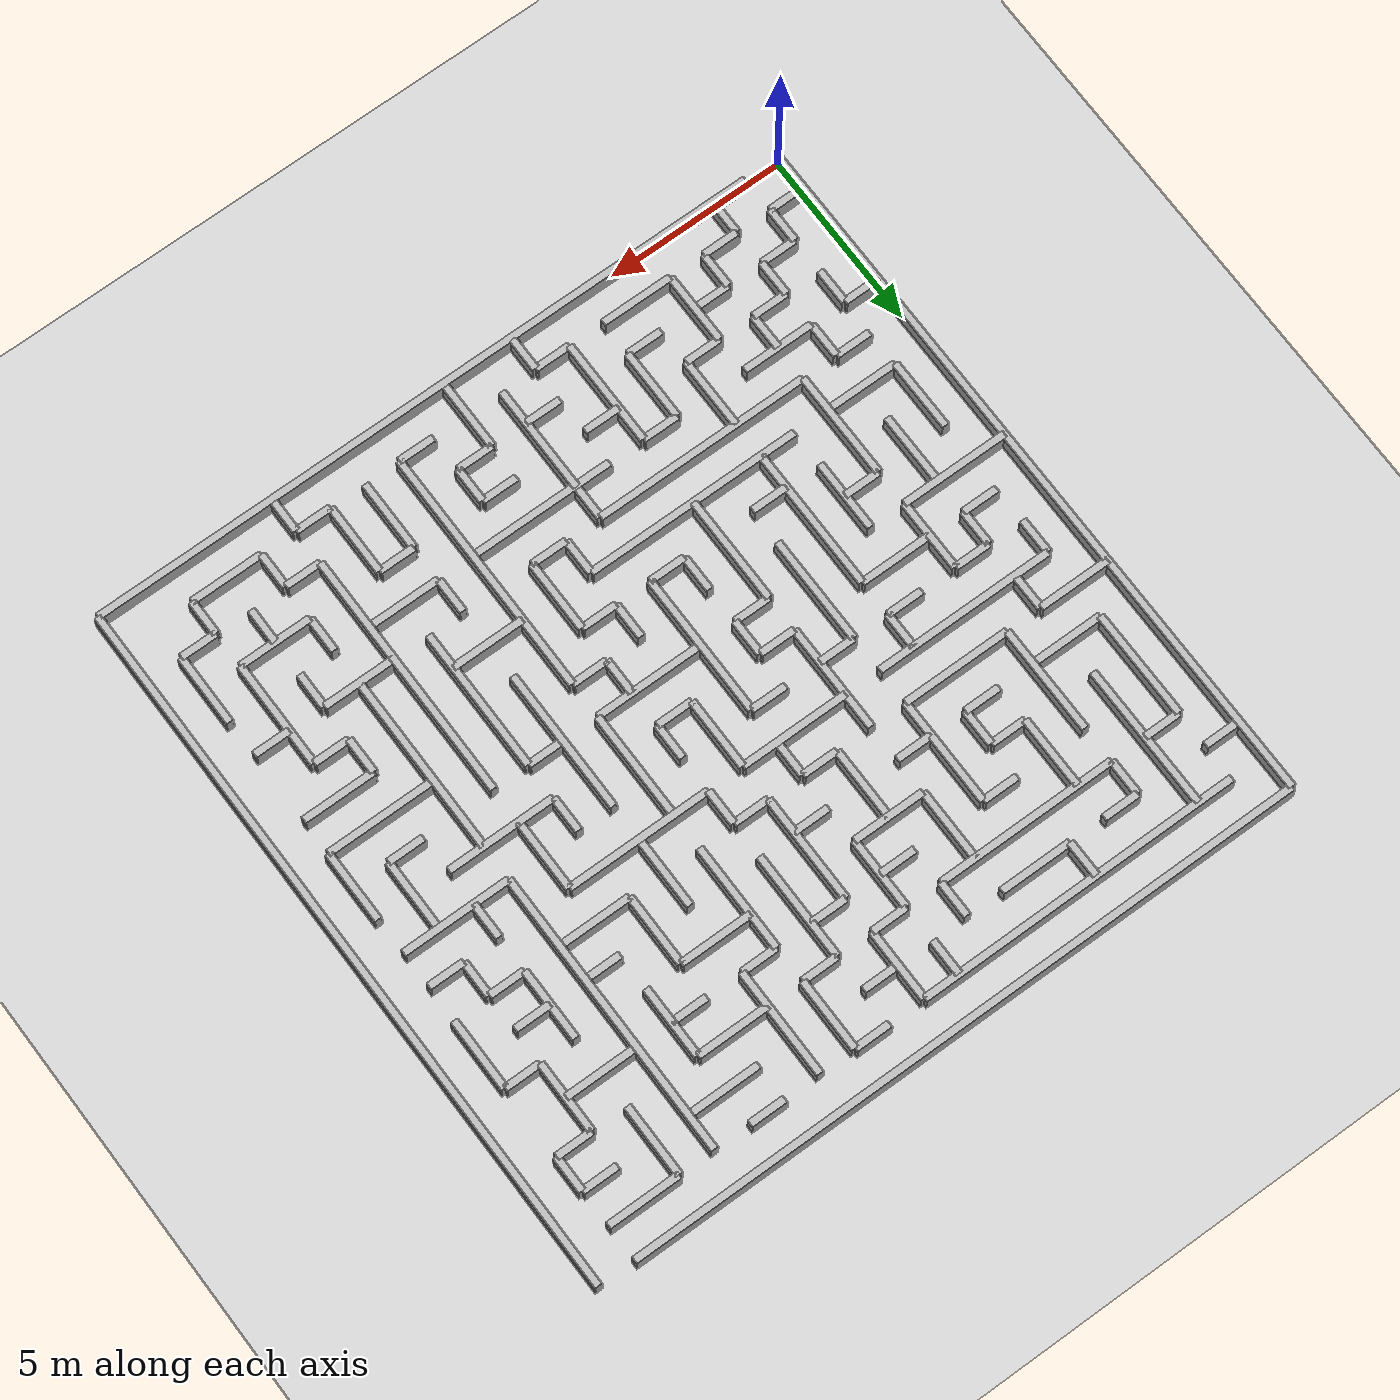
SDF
<?xml version="1.0" ?>
<sdf version="1.6">
<world name="maze_world">
  <!-- ADD these instead: -->
<light name="sun" type="directional">
  <cast_shadows>true</cast_shadows>
  <pose>0 0 10 0 0 0</pose>
  <diffuse>0.8 0.8 0.8 1</diffuse>
  <specular>0.2 0.2 0.2 1</specular>
  <direction>-0.5 0.1 -0.9</direction>
</light>

<model name="ground_plane">
  <static>true</static>
  <link name="link">
    <collision name="collision">
      <geometry><plane><normal>0 0 1</normal><size>100 100</size></plane></geometry>
    </collision>
    <visual name="visual">
      <geometry><plane><normal>0 0 1</normal><size>100 100</size></plane></geometry>
      <material><ambient>0.8 0.8 0.8 1</ambient></material>
    </visual>
  </link>
</model>

  <model name="wall_0">
    <static>true</static>
    <pose>0.5 1 0 0 0 0</pose>
    <link name="link">
      <collision name="collision">
        <geometry><box><size>1 0.2 1</size></box></geometry>
      </collision>
      <visual name="visual">
        <geometry><box><size>1 0.2 1</size></box></geometry>
        <material><ambient>0.7 0.7 0.7 1</ambient></material>
      </visual>
    </link>
  </model>
  <model name="wall_1">
    <static>true</static>
    <pose>2.5 1 0 0 0 0</pose>
    <link name="link">
      <collision name="collision">
        <geometry><box><size>1 0.2 1</size></box></geometry>
      </collision>
      <visual name="visual">
        <geometry><box><size>1 0.2 1</size></box></geometry>
        <material><ambient>0.7 0.7 0.7 1</ambient></material>
      </visual>
    </link>
  </model>
  <model name="wall_2">
    <static>true</static>
    <pose>5 1 0 0 0 0</pose>
    <link name="link">
      <collision name="collision">
        <geometry><box><size>2 0.2 1</size></box></geometry>
      </collision>
      <visual name="visual">
        <geometry><box><size>2 0.2 1</size></box></geometry>
        <material><ambient>0.7 0.7 0.7 1</ambient></material>
      </visual>
    </link>
  </model>
  <model name="wall_3">
    <static>true</static>
    <pose>7.5 1 0 0 0 0</pose>
    <link name="link">
      <collision name="collision">
        <geometry><box><size>1 0.2 1</size></box></geometry>
      </collision>
      <visual name="visual">
        <geometry><box><size>1 0.2 1</size></box></geometry>
        <material><ambient>0.7 0.7 0.7 1</ambient></material>
      </visual>
    </link>
  </model>
  <model name="wall_4">
    <static>true</static>
    <pose>11.5 1 0 0 0 0</pose>
    <link name="link">
      <collision name="collision">
        <geometry><box><size>1 0.2 1</size></box></geometry>
      </collision>
      <visual name="visual">
        <geometry><box><size>1 0.2 1</size></box></geometry>
        <material><ambient>0.7 0.7 0.7 1</ambient></material>
      </visual>
    </link>
  </model>
  <model name="wall_5">
    <static>true</static>
    <pose>14.5 1 0 0 0 0</pose>
    <link name="link">
      <collision name="collision">
        <geometry><box><size>1 0.2 1</size></box></geometry>
      </collision>
      <visual name="visual">
        <geometry><box><size>1 0.2 1</size></box></geometry>
        <material><ambient>0.7 0.7 0.7 1</ambient></material>
      </visual>
    </link>
  </model>
  <model name="wall_6">
    <static>true</static>
    <pose>17 1 0 0 0 0</pose>
    <link name="link">
      <collision name="collision">
        <geometry><box><size>2 0.2 1</size></box></geometry>
      </collision>
      <visual name="visual">
        <geometry><box><size>2 0.2 1</size></box></geometry>
        <material><ambient>0.7 0.7 0.7 1</ambient></material>
      </visual>
    </link>
  </model>
  <model name="wall_7">
    <static>true</static>
    <pose>1.5 2 0 0 0 0</pose>
    <link name="link">
      <collision name="collision">
        <geometry><box><size>1 0.2 1</size></box></geometry>
      </collision>
      <visual name="visual">
        <geometry><box><size>1 0.2 1</size></box></geometry>
        <material><ambient>0.7 0.7 0.7 1</ambient></material>
      </visual>
    </link>
  </model>
  <model name="wall_8">
    <static>true</static>
    <pose>3.5 2 0 0 0 0</pose>
    <link name="link">
      <collision name="collision">
        <geometry><box><size>1 0.2 1</size></box></geometry>
      </collision>
      <visual name="visual">
        <geometry><box><size>1 0.2 1</size></box></geometry>
        <material><ambient>0.7 0.7 0.7 1</ambient></material>
      </visual>
    </link>
  </model>
  <model name="wall_9">
    <static>true</static>
    <pose>5.5 2 0 0 0 0</pose>
    <link name="link">
      <collision name="collision">
        <geometry><box><size>1 0.2 1</size></box></geometry>
      </collision>
      <visual name="visual">
        <geometry><box><size>1 0.2 1</size></box></geometry>
        <material><ambient>0.7 0.7 0.7 1</ambient></material>
      </visual>
    </link>
  </model>
  <model name="wall_10">
    <static>true</static>
    <pose>8.5 2 0 0 0 0</pose>
    <link name="link">
      <collision name="collision">
        <geometry><box><size>1 0.2 1</size></box></geometry>
      </collision>
      <visual name="visual">
        <geometry><box><size>1 0.2 1</size></box></geometry>
        <material><ambient>0.7 0.7 0.7 1</ambient></material>
      </visual>
    </link>
  </model>
  <model name="wall_11">
    <static>true</static>
    <pose>10.5 2 0 0 0 0</pose>
    <link name="link">
      <collision name="collision">
        <geometry><box><size>1 0.2 1</size></box></geometry>
      </collision>
      <visual name="visual">
        <geometry><box><size>1 0.2 1</size></box></geometry>
        <material><ambient>0.7 0.7 0.7 1</ambient></material>
      </visual>
    </link>
  </model>
  <model name="wall_12">
    <static>true</static>
    <pose>15.5 2 0 0 0 0</pose>
    <link name="link">
      <collision name="collision">
        <geometry><box><size>1 0.2 1</size></box></geometry>
      </collision>
      <visual name="visual">
        <geometry><box><size>1 0.2 1</size></box></geometry>
        <material><ambient>0.7 0.7 0.7 1</ambient></material>
      </visual>
    </link>
  </model>
  <model name="wall_13">
    <static>true</static>
    <pose>18.5 2 0 0 0 0</pose>
    <link name="link">
      <collision name="collision">
        <geometry><box><size>1 0.2 1</size></box></geometry>
      </collision>
      <visual name="visual">
        <geometry><box><size>1 0.2 1</size></box></geometry>
        <material><ambient>0.7 0.7 0.7 1</ambient></material>
      </visual>
    </link>
  </model>
  <model name="wall_14">
    <static>true</static>
    <pose>2.5 3 0 0 0 0</pose>
    <link name="link">
      <collision name="collision">
        <geometry><box><size>1 0.2 1</size></box></geometry>
      </collision>
      <visual name="visual">
        <geometry><box><size>1 0.2 1</size></box></geometry>
        <material><ambient>0.7 0.7 0.7 1</ambient></material>
      </visual>
    </link>
  </model>
  <model name="wall_15">
    <static>true</static>
    <pose>4.5 3 0 0 0 0</pose>
    <link name="link">
      <collision name="collision">
        <geometry><box><size>1 0.2 1</size></box></geometry>
      </collision>
      <visual name="visual">
        <geometry><box><size>1 0.2 1</size></box></geometry>
        <material><ambient>0.7 0.7 0.7 1</ambient></material>
      </visual>
    </link>
  </model>
  <model name="wall_16">
    <static>true</static>
    <pose>7.5 3 0 0 0 0</pose>
    <link name="link">
      <collision name="collision">
        <geometry><box><size>1 0.2 1</size></box></geometry>
      </collision>
      <visual name="visual">
        <geometry><box><size>1 0.2 1</size></box></geometry>
        <material><ambient>0.7 0.7 0.7 1</ambient></material>
      </visual>
    </link>
  </model>
  <model name="wall_17">
    <static>true</static>
    <pose>10.5 3 0 0 0 0</pose>
    <link name="link">
      <collision name="collision">
        <geometry><box><size>1 0.2 1</size></box></geometry>
      </collision>
      <visual name="visual">
        <geometry><box><size>1 0.2 1</size></box></geometry>
        <material><ambient>0.7 0.7 0.7 1</ambient></material>
      </visual>
    </link>
  </model>
  <model name="wall_18">
    <static>true</static>
    <pose>13.5 3 0 0 0 0</pose>
    <link name="link">
      <collision name="collision">
        <geometry><box><size>1 0.2 1</size></box></geometry>
      </collision>
      <visual name="visual">
        <geometry><box><size>1 0.2 1</size></box></geometry>
        <material><ambient>0.7 0.7 0.7 1</ambient></material>
      </visual>
    </link>
  </model>
  <model name="wall_19">
    <static>true</static>
    <pose>17 3 0 0 0 0</pose>
    <link name="link">
      <collision name="collision">
        <geometry><box><size>2 0.2 1</size></box></geometry>
      </collision>
      <visual name="visual">
        <geometry><box><size>2 0.2 1</size></box></geometry>
        <material><ambient>0.7 0.7 0.7 1</ambient></material>
      </visual>
    </link>
  </model>
  <model name="wall_20">
    <static>true</static>
    <pose>0.5 4 0 0 0 0</pose>
    <link name="link">
      <collision name="collision">
        <geometry><box><size>1 0.2 1</size></box></geometry>
      </collision>
      <visual name="visual">
        <geometry><box><size>1 0.2 1</size></box></geometry>
        <material><ambient>0.7 0.7 0.7 1</ambient></material>
      </visual>
    </link>
  </model>
  <model name="wall_21">
    <static>true</static>
    <pose>3 4 0 0 0 0</pose>
    <link name="link">
      <collision name="collision">
        <geometry><box><size>2 0.2 1</size></box></geometry>
      </collision>
      <visual name="visual">
        <geometry><box><size>2 0.2 1</size></box></geometry>
        <material><ambient>0.7 0.7 0.7 1</ambient></material>
      </visual>
    </link>
  </model>
  <model name="wall_22">
    <static>true</static>
    <pose>6.5 4 0 0 0 0</pose>
    <link name="link">
      <collision name="collision">
        <geometry><box><size>1 0.2 1</size></box></geometry>
      </collision>
      <visual name="visual">
        <geometry><box><size>1 0.2 1</size></box></geometry>
        <material><ambient>0.7 0.7 0.7 1</ambient></material>
      </visual>
    </link>
  </model>
  <model name="wall_23">
    <static>true</static>
    <pose>10 4 0 0 0 0</pose>
    <link name="link">
      <collision name="collision">
        <geometry><box><size>4 0.2 1</size></box></geometry>
      </collision>
      <visual name="visual">
        <geometry><box><size>4 0.2 1</size></box></geometry>
        <material><ambient>0.7 0.7 0.7 1</ambient></material>
      </visual>
    </link>
  </model>
  <model name="wall_24">
    <static>true</static>
    <pose>14 4 0 0 0 0</pose>
    <link name="link">
      <collision name="collision">
        <geometry><box><size>2 0.2 1</size></box></geometry>
      </collision>
      <visual name="visual">
        <geometry><box><size>2 0.2 1</size></box></geometry>
        <material><ambient>0.7 0.7 0.7 1</ambient></material>
      </visual>
    </link>
  </model>
  <model name="wall_25">
    <static>true</static>
    <pose>1.5 5 0 0 0 0</pose>
    <link name="link">
      <collision name="collision">
        <geometry><box><size>1 0.2 1</size></box></geometry>
      </collision>
      <visual name="visual">
        <geometry><box><size>1 0.2 1</size></box></geometry>
        <material><ambient>0.7 0.7 0.7 1</ambient></material>
      </visual>
    </link>
  </model>
  <model name="wall_26">
    <static>true</static>
    <pose>6 5 0 0 0 0</pose>
    <link name="link">
      <collision name="collision">
        <geometry><box><size>6 0.2 1</size></box></geometry>
      </collision>
      <visual name="visual">
        <geometry><box><size>6 0.2 1</size></box></geometry>
        <material><ambient>0.7 0.7 0.7 1</ambient></material>
      </visual>
    </link>
  </model>
  <model name="wall_27">
    <static>true</static>
    <pose>10.5 5 0 0 0 0</pose>
    <link name="link">
      <collision name="collision">
        <geometry><box><size>1 0.2 1</size></box></geometry>
      </collision>
      <visual name="visual">
        <geometry><box><size>1 0.2 1</size></box></geometry>
        <material><ambient>0.7 0.7 0.7 1</ambient></material>
      </visual>
    </link>
  </model>
  <model name="wall_28">
    <static>true</static>
    <pose>16 5 0 0 0 0</pose>
    <link name="link">
      <collision name="collision">
        <geometry><box><size>2 0.2 1</size></box></geometry>
      </collision>
      <visual name="visual">
        <geometry><box><size>2 0.2 1</size></box></geometry>
        <material><ambient>0.7 0.7 0.7 1</ambient></material>
      </visual>
    </link>
  </model>
  <model name="wall_29">
    <static>true</static>
    <pose>18.5 5 0 0 0 0</pose>
    <link name="link">
      <collision name="collision">
        <geometry><box><size>1 0.2 1</size></box></geometry>
      </collision>
      <visual name="visual">
        <geometry><box><size>1 0.2 1</size></box></geometry>
        <material><ambient>0.7 0.7 0.7 1</ambient></material>
      </visual>
    </link>
  </model>
  <model name="wall_30">
    <static>true</static>
    <pose>2 6 0 0 0 0</pose>
    <link name="link">
      <collision name="collision">
        <geometry><box><size>2 0.2 1</size></box></geometry>
      </collision>
      <visual name="visual">
        <geometry><box><size>2 0.2 1</size></box></geometry>
        <material><ambient>0.7 0.7 0.7 1</ambient></material>
      </visual>
    </link>
  </model>
  <model name="wall_31">
    <static>true</static>
    <pose>7 6 0 0 0 0</pose>
    <link name="link">
      <collision name="collision">
        <geometry><box><size>6 0.2 1</size></box></geometry>
      </collision>
      <visual name="visual">
        <geometry><box><size>6 0.2 1</size></box></geometry>
        <material><ambient>0.7 0.7 0.7 1</ambient></material>
      </visual>
    </link>
  </model>
  <model name="wall_32">
    <static>true</static>
    <pose>13 6 0 0 0 0</pose>
    <link name="link">
      <collision name="collision">
        <geometry><box><size>2 0.2 1</size></box></geometry>
      </collision>
      <visual name="visual">
        <geometry><box><size>2 0.2 1</size></box></geometry>
        <material><ambient>0.7 0.7 0.7 1</ambient></material>
      </visual>
    </link>
  </model>
  <model name="wall_33">
    <static>true</static>
    <pose>17.5 6 0 0 0 0</pose>
    <link name="link">
      <collision name="collision">
        <geometry><box><size>1 0.2 1</size></box></geometry>
      </collision>
      <visual name="visual">
        <geometry><box><size>1 0.2 1</size></box></geometry>
        <material><ambient>0.7 0.7 0.7 1</ambient></material>
      </visual>
    </link>
  </model>
  <model name="wall_34">
    <static>true</static>
    <pose>5.5 7 0 0 0 0</pose>
    <link name="link">
      <collision name="collision">
        <geometry><box><size>1 0.2 1</size></box></geometry>
      </collision>
      <visual name="visual">
        <geometry><box><size>1 0.2 1</size></box></geometry>
        <material><ambient>0.7 0.7 0.7 1</ambient></material>
      </visual>
    </link>
  </model>
  <model name="wall_35">
    <static>true</static>
    <pose>8.5 7 0 0 0 0</pose>
    <link name="link">
      <collision name="collision">
        <geometry><box><size>1 0.2 1</size></box></geometry>
      </collision>
      <visual name="visual">
        <geometry><box><size>1 0.2 1</size></box></geometry>
        <material><ambient>0.7 0.7 0.7 1</ambient></material>
      </visual>
    </link>
  </model>
  <model name="wall_36">
    <static>true</static>
    <pose>10.5 7 0 0 0 0</pose>
    <link name="link">
      <collision name="collision">
        <geometry><box><size>1 0.2 1</size></box></geometry>
      </collision>
      <visual name="visual">
        <geometry><box><size>1 0.2 1</size></box></geometry>
        <material><ambient>0.7 0.7 0.7 1</ambient></material>
      </visual>
    </link>
  </model>
  <model name="wall_37">
    <static>true</static>
    <pose>18 7 0 0 0 0</pose>
    <link name="link">
      <collision name="collision">
        <geometry><box><size>2 0.2 1</size></box></geometry>
      </collision>
      <visual name="visual">
        <geometry><box><size>2 0.2 1</size></box></geometry>
        <material><ambient>0.7 0.7 0.7 1</ambient></material>
      </visual>
    </link>
  </model>
  <model name="wall_38">
    <static>true</static>
    <pose>3.5 8 0 0 0 0</pose>
    <link name="link">
      <collision name="collision">
        <geometry><box><size>1 0.2 1</size></box></geometry>
      </collision>
      <visual name="visual">
        <geometry><box><size>1 0.2 1</size></box></geometry>
        <material><ambient>0.7 0.7 0.7 1</ambient></material>
      </visual>
    </link>
  </model>
  <model name="wall_39">
    <static>true</static>
    <pose>11.5 8 0 0 0 0</pose>
    <link name="link">
      <collision name="collision">
        <geometry><box><size>1 0.2 1</size></box></geometry>
      </collision>
      <visual name="visual">
        <geometry><box><size>1 0.2 1</size></box></geometry>
        <material><ambient>0.7 0.7 0.7 1</ambient></material>
      </visual>
    </link>
  </model>
  <model name="wall_40">
    <static>true</static>
    <pose>17.5 8 0 0 0 0</pose>
    <link name="link">
      <collision name="collision">
        <geometry><box><size>3 0.2 1</size></box></geometry>
      </collision>
      <visual name="visual">
        <geometry><box><size>3 0.2 1</size></box></geometry>
        <material><ambient>0.7 0.7 0.7 1</ambient></material>
      </visual>
    </link>
  </model>
  <model name="wall_41">
    <static>true</static>
    <pose>1.5 9 0 0 0 0</pose>
    <link name="link">
      <collision name="collision">
        <geometry><box><size>3 0.2 1</size></box></geometry>
      </collision>
      <visual name="visual">
        <geometry><box><size>3 0.2 1</size></box></geometry>
        <material><ambient>0.7 0.7 0.7 1</ambient></material>
      </visual>
    </link>
  </model>
  <model name="wall_42">
    <static>true</static>
    <pose>7.5 9 0 0 0 0</pose>
    <link name="link">
      <collision name="collision">
        <geometry><box><size>1 0.2 1</size></box></geometry>
      </collision>
      <visual name="visual">
        <geometry><box><size>1 0.2 1</size></box></geometry>
        <material><ambient>0.7 0.7 0.7 1</ambient></material>
      </visual>
    </link>
  </model>
  <model name="wall_43">
    <static>true</static>
    <pose>10.5 9 0 0 0 0</pose>
    <link name="link">
      <collision name="collision">
        <geometry><box><size>3 0.2 1</size></box></geometry>
      </collision>
      <visual name="visual">
        <geometry><box><size>3 0.2 1</size></box></geometry>
        <material><ambient>0.7 0.7 0.7 1</ambient></material>
      </visual>
    </link>
  </model>
  <model name="wall_44">
    <static>true</static>
    <pose>13.5 9 0 0 0 0</pose>
    <link name="link">
      <collision name="collision">
        <geometry><box><size>1 0.2 1</size></box></geometry>
      </collision>
      <visual name="visual">
        <geometry><box><size>1 0.2 1</size></box></geometry>
        <material><ambient>0.7 0.7 0.7 1</ambient></material>
      </visual>
    </link>
  </model>
  <model name="wall_45">
    <static>true</static>
    <pose>17.5 9 0 0 0 0</pose>
    <link name="link">
      <collision name="collision">
        <geometry><box><size>1 0.2 1</size></box></geometry>
      </collision>
      <visual name="visual">
        <geometry><box><size>1 0.2 1</size></box></geometry>
        <material><ambient>0.7 0.7 0.7 1</ambient></material>
      </visual>
    </link>
  </model>
  <model name="wall_46">
    <static>true</static>
    <pose>1.5 10 0 0 0 0</pose>
    <link name="link">
      <collision name="collision">
        <geometry><box><size>1 0.2 1</size></box></geometry>
      </collision>
      <visual name="visual">
        <geometry><box><size>1 0.2 1</size></box></geometry>
        <material><ambient>0.7 0.7 0.7 1</ambient></material>
      </visual>
    </link>
  </model>
  <model name="wall_47">
    <static>true</static>
    <pose>4 10 0 0 0 0</pose>
    <link name="link">
      <collision name="collision">
        <geometry><box><size>2 0.2 1</size></box></geometry>
      </collision>
      <visual name="visual">
        <geometry><box><size>2 0.2 1</size></box></geometry>
        <material><ambient>0.7 0.7 0.7 1</ambient></material>
      </visual>
    </link>
  </model>
  <model name="wall_48">
    <static>true</static>
    <pose>7.5 10 0 0 0 0</pose>
    <link name="link">
      <collision name="collision">
        <geometry><box><size>1 0.2 1</size></box></geometry>
      </collision>
      <visual name="visual">
        <geometry><box><size>1 0.2 1</size></box></geometry>
        <material><ambient>0.7 0.7 0.7 1</ambient></material>
      </visual>
    </link>
  </model>
  <model name="wall_49">
    <static>true</static>
    <pose>10.5 10 0 0 0 0</pose>
    <link name="link">
      <collision name="collision">
        <geometry><box><size>1 0.2 1</size></box></geometry>
      </collision>
      <visual name="visual">
        <geometry><box><size>1 0.2 1</size></box></geometry>
        <material><ambient>0.7 0.7 0.7 1</ambient></material>
      </visual>
    </link>
  </model>
  <model name="wall_50">
    <static>true</static>
    <pose>15.5 10 0 0 0 0</pose>
    <link name="link">
      <collision name="collision">
        <geometry><box><size>3 0.2 1</size></box></geometry>
      </collision>
      <visual name="visual">
        <geometry><box><size>3 0.2 1</size></box></geometry>
        <material><ambient>0.7 0.7 0.7 1</ambient></material>
      </visual>
    </link>
  </model>
  <model name="wall_51">
    <static>true</static>
    <pose>2.5 11 0 0 0 0</pose>
    <link name="link">
      <collision name="collision">
        <geometry><box><size>1 0.2 1</size></box></geometry>
      </collision>
      <visual name="visual">
        <geometry><box><size>1 0.2 1</size></box></geometry>
        <material><ambient>0.7 0.7 0.7 1</ambient></material>
      </visual>
    </link>
  </model>
  <model name="wall_52">
    <static>true</static>
    <pose>4.5 11 0 0 0 0</pose>
    <link name="link">
      <collision name="collision">
        <geometry><box><size>1 0.2 1</size></box></geometry>
      </collision>
      <visual name="visual">
        <geometry><box><size>1 0.2 1</size></box></geometry>
        <material><ambient>0.7 0.7 0.7 1</ambient></material>
      </visual>
    </link>
  </model>
  <model name="wall_53">
    <static>true</static>
    <pose>6.5 11 0 0 0 0</pose>
    <link name="link">
      <collision name="collision">
        <geometry><box><size>1 0.2 1</size></box></geometry>
      </collision>
      <visual name="visual">
        <geometry><box><size>1 0.2 1</size></box></geometry>
        <material><ambient>0.7 0.7 0.7 1</ambient></material>
      </visual>
    </link>
  </model>
  <model name="wall_54">
    <static>true</static>
    <pose>8.5 11 0 0 0 0</pose>
    <link name="link">
      <collision name="collision">
        <geometry><box><size>1 0.2 1</size></box></geometry>
      </collision>
      <visual name="visual">
        <geometry><box><size>1 0.2 1</size></box></geometry>
        <material><ambient>0.7 0.7 0.7 1</ambient></material>
      </visual>
    </link>
  </model>
  <model name="wall_55">
    <static>true</static>
    <pose>17.5 11 0 0 0 0</pose>
    <link name="link">
      <collision name="collision">
        <geometry><box><size>3 0.2 1</size></box></geometry>
      </collision>
      <visual name="visual">
        <geometry><box><size>3 0.2 1</size></box></geometry>
        <material><ambient>0.7 0.7 0.7 1</ambient></material>
      </visual>
    </link>
  </model>
  <model name="wall_56">
    <static>true</static>
    <pose>3.5 12 0 0 0 0</pose>
    <link name="link">
      <collision name="collision">
        <geometry><box><size>5 0.2 1</size></box></geometry>
      </collision>
      <visual name="visual">
        <geometry><box><size>5 0.2 1</size></box></geometry>
        <material><ambient>0.7 0.7 0.7 1</ambient></material>
      </visual>
    </link>
  </model>
  <model name="wall_57">
    <static>true</static>
    <pose>8.5 12 0 0 0 0</pose>
    <link name="link">
      <collision name="collision">
        <geometry><box><size>3 0.2 1</size></box></geometry>
      </collision>
      <visual name="visual">
        <geometry><box><size>3 0.2 1</size></box></geometry>
        <material><ambient>0.7 0.7 0.7 1</ambient></material>
      </visual>
    </link>
  </model>
  <model name="wall_58">
    <static>true</static>
    <pose>13 12 0 0 0 0</pose>
    <link name="link">
      <collision name="collision">
        <geometry><box><size>4 0.2 1</size></box></geometry>
      </collision>
      <visual name="visual">
        <geometry><box><size>4 0.2 1</size></box></geometry>
        <material><ambient>0.7 0.7 0.7 1</ambient></material>
      </visual>
    </link>
  </model>
  <model name="wall_59">
    <static>true</static>
    <pose>18.5 12 0 0 0 0</pose>
    <link name="link">
      <collision name="collision">
        <geometry><box><size>1 0.2 1</size></box></geometry>
      </collision>
      <visual name="visual">
        <geometry><box><size>1 0.2 1</size></box></geometry>
        <material><ambient>0.7 0.7 0.7 1</ambient></material>
      </visual>
    </link>
  </model>
  <model name="wall_60">
    <static>true</static>
    <pose>1 13 0 0 0 0</pose>
    <link name="link">
      <collision name="collision">
        <geometry><box><size>2 0.2 1</size></box></geometry>
      </collision>
      <visual name="visual">
        <geometry><box><size>2 0.2 1</size></box></geometry>
        <material><ambient>0.7 0.7 0.7 1</ambient></material>
      </visual>
    </link>
  </model>
  <model name="wall_61">
    <static>true</static>
    <pose>4.5 13 0 0 0 0</pose>
    <link name="link">
      <collision name="collision">
        <geometry><box><size>3 0.2 1</size></box></geometry>
      </collision>
      <visual name="visual">
        <geometry><box><size>3 0.2 1</size></box></geometry>
        <material><ambient>0.7 0.7 0.7 1</ambient></material>
      </visual>
    </link>
  </model>
  <model name="wall_62">
    <static>true</static>
    <pose>8.5 13 0 0 0 0</pose>
    <link name="link">
      <collision name="collision">
        <geometry><box><size>1 0.2 1</size></box></geometry>
      </collision>
      <visual name="visual">
        <geometry><box><size>1 0.2 1</size></box></geometry>
        <material><ambient>0.7 0.7 0.7 1</ambient></material>
      </visual>
    </link>
  </model>
  <model name="wall_63">
    <static>true</static>
    <pose>10.5 13 0 0 0 0</pose>
    <link name="link">
      <collision name="collision">
        <geometry><box><size>1 0.2 1</size></box></geometry>
      </collision>
      <visual name="visual">
        <geometry><box><size>1 0.2 1</size></box></geometry>
        <material><ambient>0.7 0.7 0.7 1</ambient></material>
      </visual>
    </link>
  </model>
  <model name="wall_64">
    <static>true</static>
    <pose>15 13 0 0 0 0</pose>
    <link name="link">
      <collision name="collision">
        <geometry><box><size>2 0.2 1</size></box></geometry>
      </collision>
      <visual name="visual">
        <geometry><box><size>2 0.2 1</size></box></geometry>
        <material><ambient>0.7 0.7 0.7 1</ambient></material>
      </visual>
    </link>
  </model>
  <model name="wall_65">
    <static>true</static>
    <pose>17.5 13 0 0 0 0</pose>
    <link name="link">
      <collision name="collision">
        <geometry><box><size>1 0.2 1</size></box></geometry>
      </collision>
      <visual name="visual">
        <geometry><box><size>1 0.2 1</size></box></geometry>
        <material><ambient>0.7 0.7 0.7 1</ambient></material>
      </visual>
    </link>
  </model>
  <model name="wall_66">
    <static>true</static>
    <pose>2 14 0 0 0 0</pose>
    <link name="link">
      <collision name="collision">
        <geometry><box><size>2 0.2 1</size></box></geometry>
      </collision>
      <visual name="visual">
        <geometry><box><size>2 0.2 1</size></box></geometry>
        <material><ambient>0.7 0.7 0.7 1</ambient></material>
      </visual>
    </link>
  </model>
  <model name="wall_67">
    <static>true</static>
    <pose>4.5 14 0 0 0 0</pose>
    <link name="link">
      <collision name="collision">
        <geometry><box><size>1 0.2 1</size></box></geometry>
      </collision>
      <visual name="visual">
        <geometry><box><size>1 0.2 1</size></box></geometry>
        <material><ambient>0.7 0.7 0.7 1</ambient></material>
      </visual>
    </link>
  </model>
  <model name="wall_68">
    <static>true</static>
    <pose>6.5 14 0 0 0 0</pose>
    <link name="link">
      <collision name="collision">
        <geometry><box><size>1 0.2 1</size></box></geometry>
      </collision>
      <visual name="visual">
        <geometry><box><size>1 0.2 1</size></box></geometry>
        <material><ambient>0.7 0.7 0.7 1</ambient></material>
      </visual>
    </link>
  </model>
  <model name="wall_69">
    <static>true</static>
    <pose>9.5 14 0 0 0 0</pose>
    <link name="link">
      <collision name="collision">
        <geometry><box><size>1 0.2 1</size></box></geometry>
      </collision>
      <visual name="visual">
        <geometry><box><size>1 0.2 1</size></box></geometry>
        <material><ambient>0.7 0.7 0.7 1</ambient></material>
      </visual>
    </link>
  </model>
  <model name="wall_70">
    <static>true</static>
    <pose>15.5 14 0 0 0 0</pose>
    <link name="link">
      <collision name="collision">
        <geometry><box><size>1 0.2 1</size></box></geometry>
      </collision>
      <visual name="visual">
        <geometry><box><size>1 0.2 1</size></box></geometry>
        <material><ambient>0.7 0.7 0.7 1</ambient></material>
      </visual>
    </link>
  </model>
  <model name="wall_71">
    <static>true</static>
    <pose>17.5 14 0 0 0 0</pose>
    <link name="link">
      <collision name="collision">
        <geometry><box><size>1 0.2 1</size></box></geometry>
      </collision>
      <visual name="visual">
        <geometry><box><size>1 0.2 1</size></box></geometry>
        <material><ambient>0.7 0.7 0.7 1</ambient></material>
      </visual>
    </link>
  </model>
  <model name="wall_72">
    <static>true</static>
    <pose>4.5 15 0 0 0 0</pose>
    <link name="link">
      <collision name="collision">
        <geometry><box><size>1 0.2 1</size></box></geometry>
      </collision>
      <visual name="visual">
        <geometry><box><size>1 0.2 1</size></box></geometry>
        <material><ambient>0.7 0.7 0.7 1</ambient></material>
      </visual>
    </link>
  </model>
  <model name="wall_73">
    <static>true</static>
    <pose>8 15 0 0 0 0</pose>
    <link name="link">
      <collision name="collision">
        <geometry><box><size>2 0.2 1</size></box></geometry>
      </collision>
      <visual name="visual">
        <geometry><box><size>2 0.2 1</size></box></geometry>
        <material><ambient>0.7 0.7 0.7 1</ambient></material>
      </visual>
    </link>
  </model>
  <model name="wall_74">
    <static>true</static>
    <pose>13 15 0 0 0 0</pose>
    <link name="link">
      <collision name="collision">
        <geometry><box><size>2 0.2 1</size></box></geometry>
      </collision>
      <visual name="visual">
        <geometry><box><size>2 0.2 1</size></box></geometry>
        <material><ambient>0.7 0.7 0.7 1</ambient></material>
      </visual>
    </link>
  </model>
  <model name="wall_75">
    <static>true</static>
    <pose>18.5 15 0 0 0 0</pose>
    <link name="link">
      <collision name="collision">
        <geometry><box><size>1 0.2 1</size></box></geometry>
      </collision>
      <visual name="visual">
        <geometry><box><size>1 0.2 1</size></box></geometry>
        <material><ambient>0.7 0.7 0.7 1</ambient></material>
      </visual>
    </link>
  </model>
  <model name="wall_76">
    <static>true</static>
    <pose>5.5 16 0 0 0 0</pose>
    <link name="link">
      <collision name="collision">
        <geometry><box><size>1 0.2 1</size></box></geometry>
      </collision>
      <visual name="visual">
        <geometry><box><size>1 0.2 1</size></box></geometry>
        <material><ambient>0.7 0.7 0.7 1</ambient></material>
      </visual>
    </link>
  </model>
  <model name="wall_77">
    <static>true</static>
    <pose>8.5 16 0 0 0 0</pose>
    <link name="link">
      <collision name="collision">
        <geometry><box><size>1 0.2 1</size></box></geometry>
      </collision>
      <visual name="visual">
        <geometry><box><size>1 0.2 1</size></box></geometry>
        <material><ambient>0.7 0.7 0.7 1</ambient></material>
      </visual>
    </link>
  </model>
  <model name="wall_78">
    <static>true</static>
    <pose>10.5 16 0 0 0 0</pose>
    <link name="link">
      <collision name="collision">
        <geometry><box><size>1 0.2 1</size></box></geometry>
      </collision>
      <visual name="visual">
        <geometry><box><size>1 0.2 1</size></box></geometry>
        <material><ambient>0.7 0.7 0.7 1</ambient></material>
      </visual>
    </link>
  </model>
  <model name="wall_79">
    <static>true</static>
    <pose>12.5 16 0 0 0 0</pose>
    <link name="link">
      <collision name="collision">
        <geometry><box><size>1 0.2 1</size></box></geometry>
      </collision>
      <visual name="visual">
        <geometry><box><size>1 0.2 1</size></box></geometry>
        <material><ambient>0.7 0.7 0.7 1</ambient></material>
      </visual>
    </link>
  </model>
  <model name="wall_80">
    <static>true</static>
    <pose>14.5 16 0 0 0 0</pose>
    <link name="link">
      <collision name="collision">
        <geometry><box><size>1 0.2 1</size></box></geometry>
      </collision>
      <visual name="visual">
        <geometry><box><size>1 0.2 1</size></box></geometry>
        <material><ambient>0.7 0.7 0.7 1</ambient></material>
      </visual>
    </link>
  </model>
  <model name="wall_81">
    <static>true</static>
    <pose>17 16 0 0 0 0</pose>
    <link name="link">
      <collision name="collision">
        <geometry><box><size>2 0.2 1</size></box></geometry>
      </collision>
      <visual name="visual">
        <geometry><box><size>2 0.2 1</size></box></geometry>
        <material><ambient>0.7 0.7 0.7 1</ambient></material>
      </visual>
    </link>
  </model>
  <model name="wall_82">
    <static>true</static>
    <pose>1.5 17 0 0 0 0</pose>
    <link name="link">
      <collision name="collision">
        <geometry><box><size>1 0.2 1</size></box></geometry>
      </collision>
      <visual name="visual">
        <geometry><box><size>1 0.2 1</size></box></geometry>
        <material><ambient>0.7 0.7 0.7 1</ambient></material>
      </visual>
    </link>
  </model>
  <model name="wall_83">
    <static>true</static>
    <pose>5.5 17 0 0 0 0</pose>
    <link name="link">
      <collision name="collision">
        <geometry><box><size>5 0.2 1</size></box></geometry>
      </collision>
      <visual name="visual">
        <geometry><box><size>5 0.2 1</size></box></geometry>
        <material><ambient>0.7 0.7 0.7 1</ambient></material>
      </visual>
    </link>
  </model>
  <model name="wall_84">
    <static>true</static>
    <pose>9.5 17 0 0 0 0</pose>
    <link name="link">
      <collision name="collision">
        <geometry><box><size>1 0.2 1</size></box></geometry>
      </collision>
      <visual name="visual">
        <geometry><box><size>1 0.2 1</size></box></geometry>
        <material><ambient>0.7 0.7 0.7 1</ambient></material>
      </visual>
    </link>
  </model>
  <model name="wall_85">
    <static>true</static>
    <pose>11.5 17 0 0 0 0</pose>
    <link name="link">
      <collision name="collision">
        <geometry><box><size>1 0.2 1</size></box></geometry>
      </collision>
      <visual name="visual">
        <geometry><box><size>1 0.2 1</size></box></geometry>
        <material><ambient>0.7 0.7 0.7 1</ambient></material>
      </visual>
    </link>
  </model>
  <model name="wall_86">
    <static>true</static>
    <pose>14 17 0 0 0 0</pose>
    <link name="link">
      <collision name="collision">
        <geometry><box><size>2 0.2 1</size></box></geometry>
      </collision>
      <visual name="visual">
        <geometry><box><size>2 0.2 1</size></box></geometry>
        <material><ambient>0.7 0.7 0.7 1</ambient></material>
      </visual>
    </link>
  </model>
  <model name="wall_87">
    <static>true</static>
    <pose>18.5 17 0 0 0 0</pose>
    <link name="link">
      <collision name="collision">
        <geometry><box><size>1 0.2 1</size></box></geometry>
      </collision>
      <visual name="visual">
        <geometry><box><size>1 0.2 1</size></box></geometry>
        <material><ambient>0.7 0.7 0.7 1</ambient></material>
      </visual>
    </link>
  </model>
  <model name="wall_88">
    <static>true</static>
    <pose>0.5 18 0 0 0 0</pose>
    <link name="link">
      <collision name="collision">
        <geometry><box><size>1 0.2 1</size></box></geometry>
      </collision>
      <visual name="visual">
        <geometry><box><size>1 0.2 1</size></box></geometry>
        <material><ambient>0.7 0.7 0.7 1</ambient></material>
      </visual>
    </link>
  </model>
  <model name="wall_89">
    <static>true</static>
    <pose>3.5 18 0 0 0 0</pose>
    <link name="link">
      <collision name="collision">
        <geometry><box><size>1 0.2 1</size></box></geometry>
      </collision>
      <visual name="visual">
        <geometry><box><size>1 0.2 1</size></box></geometry>
        <material><ambient>0.7 0.7 0.7 1</ambient></material>
      </visual>
    </link>
  </model>
  <model name="wall_90">
    <static>true</static>
    <pose>6 18 0 0 0 0</pose>
    <link name="link">
      <collision name="collision">
        <geometry><box><size>2 0.2 1</size></box></geometry>
      </collision>
      <visual name="visual">
        <geometry><box><size>2 0.2 1</size></box></geometry>
        <material><ambient>0.7 0.7 0.7 1</ambient></material>
      </visual>
    </link>
  </model>
  <model name="wall_91">
    <static>true</static>
    <pose>10.5 18 0 0 0 0</pose>
    <link name="link">
      <collision name="collision">
        <geometry><box><size>1 0.2 1</size></box></geometry>
      </collision>
      <visual name="visual">
        <geometry><box><size>1 0.2 1</size></box></geometry>
        <material><ambient>0.7 0.7 0.7 1</ambient></material>
      </visual>
    </link>
  </model>
  <model name="wall_92">
    <static>true</static>
    <pose>15 18 0 0 0 0</pose>
    <link name="link">
      <collision name="collision">
        <geometry><box><size>2 0.2 1</size></box></geometry>
      </collision>
      <visual name="visual">
        <geometry><box><size>2 0.2 1</size></box></geometry>
        <material><ambient>0.7 0.7 0.7 1</ambient></material>
      </visual>
    </link>
  </model>
  <model name="wall_93">
    <static>true</static>
    <pose>18.5 18 0 0 0 0</pose>
    <link name="link">
      <collision name="collision">
        <geometry><box><size>1 0.2 1</size></box></geometry>
      </collision>
      <visual name="visual">
        <geometry><box><size>1 0.2 1</size></box></geometry>
        <material><ambient>0.7 0.7 0.7 1</ambient></material>
      </visual>
    </link>
  </model>
  <model name="wall_94">
    <static>true</static>
    <pose>5.5 19 0 0 0 0</pose>
    <link name="link">
      <collision name="collision">
        <geometry><box><size>9 0.2 1</size></box></geometry>
      </collision>
      <visual name="visual">
        <geometry><box><size>9 0.2 1</size></box></geometry>
        <material><ambient>0.7 0.7 0.7 1</ambient></material>
      </visual>
    </link>
  </model>
  <model name="wall_95">
    <static>true</static>
    <pose>11.5 19 0 0 0 0</pose>
    <link name="link">
      <collision name="collision">
        <geometry><box><size>1 0.2 1</size></box></geometry>
      </collision>
      <visual name="visual">
        <geometry><box><size>1 0.2 1</size></box></geometry>
        <material><ambient>0.7 0.7 0.7 1</ambient></material>
      </visual>
    </link>
  </model>
  <model name="wall_96">
    <static>true</static>
    <pose>14.5 19 0 0 0 0</pose>
    <link name="link">
      <collision name="collision">
        <geometry><box><size>1 0.2 1</size></box></geometry>
      </collision>
      <visual name="visual">
        <geometry><box><size>1 0.2 1</size></box></geometry>
        <material><ambient>0.7 0.7 0.7 1</ambient></material>
      </visual>
    </link>
  </model>
  <model name="wall_97">
    <static>true</static>
    <pose>18 19 0 0 0 0</pose>
    <link name="link">
      <collision name="collision">
        <geometry><box><size>2 0.2 1</size></box></geometry>
      </collision>
      <visual name="visual">
        <geometry><box><size>2 0.2 1</size></box></geometry>
        <material><ambient>0.7 0.7 0.7 1</ambient></material>
      </visual>
    </link>
  </model>
  <model name="wall_98">
    <static>true</static>
    <pose>1 1.5 0 0 0 0</pose>
    <link name="link">
      <collision name="collision">
        <geometry><box><size>0.2 1 1</size></box></geometry>
      </collision>
      <visual name="visual">
        <geometry><box><size>0.2 1 1</size></box></geometry>
        <material><ambient>0.7 0.7 0.7 1</ambient></material>
      </visual>
    </link>
  </model>
  <model name="wall_99">
    <static>true</static>
    <pose>1 3.5 0 0 0 0</pose>
    <link name="link">
      <collision name="collision">
        <geometry><box><size>0.2 1 1</size></box></geometry>
      </collision>
      <visual name="visual">
        <geometry><box><size>0.2 1 1</size></box></geometry>
        <material><ambient>0.7 0.7 0.7 1</ambient></material>
      </visual>
    </link>
  </model>
  <model name="wall_100">
    <static>true</static>
    <pose>1 7 0 0 0 0</pose>
    <link name="link">
      <collision name="collision">
        <geometry><box><size>0.2 2 1</size></box></geometry>
      </collision>
      <visual name="visual">
        <geometry><box><size>0.2 2 1</size></box></geometry>
        <material><ambient>0.7 0.7 0.7 1</ambient></material>
      </visual>
    </link>
  </model>
  <model name="wall_101">
    <static>true</static>
    <pose>1 11.5 0 0 0 0</pose>
    <link name="link">
      <collision name="collision">
        <geometry><box><size>0.2 1 1</size></box></geometry>
      </collision>
      <visual name="visual">
        <geometry><box><size>0.2 1 1</size></box></geometry>
        <material><ambient>0.7 0.7 0.7 1</ambient></material>
      </visual>
    </link>
  </model>
  <model name="wall_102">
    <static>true</static>
    <pose>1 15.5 0 0 0 0</pose>
    <link name="link">
      <collision name="collision">
        <geometry><box><size>0.2 3 1</size></box></geometry>
      </collision>
      <visual name="visual">
        <geometry><box><size>0.2 3 1</size></box></geometry>
        <material><ambient>0.7 0.7 0.7 1</ambient></material>
      </visual>
    </link>
  </model>
  <model name="wall_103">
    <static>true</static>
    <pose>2 0.5 0 0 0 0</pose>
    <link name="link">
      <collision name="collision">
        <geometry><box><size>0.2 1 1</size></box></geometry>
      </collision>
      <visual name="visual">
        <geometry><box><size>0.2 1 1</size></box></geometry>
        <material><ambient>0.7 0.7 0.7 1</ambient></material>
      </visual>
    </link>
  </model>
  <model name="wall_104">
    <static>true</static>
    <pose>2 2.5 0 0 0 0</pose>
    <link name="link">
      <collision name="collision">
        <geometry><box><size>0.2 1 1</size></box></geometry>
      </collision>
      <visual name="visual">
        <geometry><box><size>0.2 1 1</size></box></geometry>
        <material><ambient>0.7 0.7 0.7 1</ambient></material>
      </visual>
    </link>
  </model>
  <model name="wall_105">
    <static>true</static>
    <pose>2 4.5 0 0 0 0</pose>
    <link name="link">
      <collision name="collision">
        <geometry><box><size>0.2 1 1</size></box></geometry>
      </collision>
      <visual name="visual">
        <geometry><box><size>0.2 1 1</size></box></geometry>
        <material><ambient>0.7 0.7 0.7 1</ambient></material>
      </visual>
    </link>
  </model>
  <model name="wall_106">
    <static>true</static>
    <pose>2 8 0 0 0 0</pose>
    <link name="link">
      <collision name="collision">
        <geometry><box><size>0.2 2 1</size></box></geometry>
      </collision>
      <visual name="visual">
        <geometry><box><size>0.2 2 1</size></box></geometry>
        <material><ambient>0.7 0.7 0.7 1</ambient></material>
      </visual>
    </link>
  </model>
  <model name="wall_107">
    <static>true</static>
    <pose>2 10.5 0 0 0 0</pose>
    <link name="link">
      <collision name="collision">
        <geometry><box><size>0.2 1 1</size></box></geometry>
      </collision>
      <visual name="visual">
        <geometry><box><size>0.2 1 1</size></box></geometry>
        <material><ambient>0.7 0.7 0.7 1</ambient></material>
      </visual>
    </link>
  </model>
  <model name="wall_108">
    <static>true</static>
    <pose>2 12.5 0 0 0 0</pose>
    <link name="link">
      <collision name="collision">
        <geometry><box><size>0.2 1 1</size></box></geometry>
      </collision>
      <visual name="visual">
        <geometry><box><size>0.2 1 1</size></box></geometry>
        <material><ambient>0.7 0.7 0.7 1</ambient></material>
      </visual>
    </link>
  </model>
  <model name="wall_109">
    <static>true</static>
    <pose>2 17 0 0 0 0</pose>
    <link name="link">
      <collision name="collision">
        <geometry><box><size>0.2 4 1</size></box></geometry>
      </collision>
      <visual name="visual">
        <geometry><box><size>0.2 4 1</size></box></geometry>
        <material><ambient>0.7 0.7 0.7 1</ambient></material>
      </visual>
    </link>
  </model>
  <model name="wall_110">
    <static>true</static>
    <pose>3 1.5 0 0 0 0</pose>
    <link name="link">
      <collision name="collision">
        <geometry><box><size>0.2 1 1</size></box></geometry>
      </collision>
      <visual name="visual">
        <geometry><box><size>0.2 1 1</size></box></geometry>
        <material><ambient>0.7 0.7 0.7 1</ambient></material>
      </visual>
    </link>
  </model>
  <model name="wall_111">
    <static>true</static>
    <pose>3 3.5 0 0 0 0</pose>
    <link name="link">
      <collision name="collision">
        <geometry><box><size>0.2 1 1</size></box></geometry>
      </collision>
      <visual name="visual">
        <geometry><box><size>0.2 1 1</size></box></geometry>
        <material><ambient>0.7 0.7 0.7 1</ambient></material>
      </visual>
    </link>
  </model>
  <model name="wall_112">
    <static>true</static>
    <pose>3 6.5 0 0 0 0</pose>
    <link name="link">
      <collision name="collision">
        <geometry><box><size>0.2 3 1</size></box></geometry>
      </collision>
      <visual name="visual">
        <geometry><box><size>0.2 3 1</size></box></geometry>
        <material><ambient>0.7 0.7 0.7 1</ambient></material>
      </visual>
    </link>
  </model>
  <model name="wall_113">
    <static>true</static>
    <pose>3 10 0 0 0 0</pose>
    <link name="link">
      <collision name="collision">
        <geometry><box><size>0.2 2 1</size></box></geometry>
      </collision>
      <visual name="visual">
        <geometry><box><size>0.2 2 1</size></box></geometry>
        <material><ambient>0.7 0.7 0.7 1</ambient></material>
      </visual>
    </link>
  </model>
  <model name="wall_114">
    <static>true</static>
    <pose>3 14.5 0 0 0 0</pose>
    <link name="link">
      <collision name="collision">
        <geometry><box><size>0.2 3 1</size></box></geometry>
      </collision>
      <visual name="visual">
        <geometry><box><size>0.2 3 1</size></box></geometry>
        <material><ambient>0.7 0.7 0.7 1</ambient></material>
      </visual>
    </link>
  </model>
  <model name="wall_115">
    <static>true</static>
    <pose>3 17.5 0 0 0 0</pose>
    <link name="link">
      <collision name="collision">
        <geometry><box><size>0.2 1 1</size></box></geometry>
      </collision>
      <visual name="visual">
        <geometry><box><size>0.2 1 1</size></box></geometry>
        <material><ambient>0.7 0.7 0.7 1</ambient></material>
      </visual>
    </link>
  </model>
  <model name="wall_116">
    <static>true</static>
    <pose>4 2 0 0 0 0</pose>
    <link name="link">
      <collision name="collision">
        <geometry><box><size>0.2 2 1</size></box></geometry>
      </collision>
      <visual name="visual">
        <geometry><box><size>0.2 2 1</size></box></geometry>
        <material><ambient>0.7 0.7 0.7 1</ambient></material>
      </visual>
    </link>
  </model>
  <model name="wall_117">
    <static>true</static>
    <pose>4 8 0 0 0 0</pose>
    <link name="link">
      <collision name="collision">
        <geometry><box><size>0.2 2 1</size></box></geometry>
      </collision>
      <visual name="visual">
        <geometry><box><size>0.2 2 1</size></box></geometry>
        <material><ambient>0.7 0.7 0.7 1</ambient></material>
      </visual>
    </link>
  </model>
  <model name="wall_118">
    <static>true</static>
    <pose>4 16 0 0 0 0</pose>
    <link name="link">
      <collision name="collision">
        <geometry><box><size>0.2 2 1</size></box></geometry>
      </collision>
      <visual name="visual">
        <geometry><box><size>0.2 2 1</size></box></geometry>
        <material><ambient>0.7 0.7 0.7 1</ambient></material>
      </visual>
    </link>
  </model>
  <model name="wall_119">
    <static>true</static>
    <pose>5 4 0 0 0 0</pose>
    <link name="link">
      <collision name="collision">
        <geometry><box><size>0.2 2 1</size></box></geometry>
      </collision>
      <visual name="visual">
        <geometry><box><size>0.2 2 1</size></box></geometry>
        <material><ambient>0.7 0.7 0.7 1</ambient></material>
      </visual>
    </link>
  </model>
  <model name="wall_120">
    <static>true</static>
    <pose>5 8 0 0 0 0</pose>
    <link name="link">
      <collision name="collision">
        <geometry><box><size>0.2 4 1</size></box></geometry>
      </collision>
      <visual name="visual">
        <geometry><box><size>0.2 4 1</size></box></geometry>
        <material><ambient>0.7 0.7 0.7 1</ambient></material>
      </visual>
    </link>
  </model>
  <model name="wall_121">
    <static>true</static>
    <pose>5 11.5 0 0 0 0</pose>
    <link name="link">
      <collision name="collision">
        <geometry><box><size>0.2 1 1</size></box></geometry>
      </collision>
      <visual name="visual">
        <geometry><box><size>0.2 1 1</size></box></geometry>
        <material><ambient>0.7 0.7 0.7 1</ambient></material>
      </visual>
    </link>
  </model>
  <model name="wall_122">
    <static>true</static>
    <pose>5 14.5 0 0 0 0</pose>
    <link name="link">
      <collision name="collision">
        <geometry><box><size>0.2 1 1</size></box></geometry>
      </collision>
      <visual name="visual">
        <geometry><box><size>0.2 1 1</size></box></geometry>
        <material><ambient>0.7 0.7 0.7 1</ambient></material>
      </visual>
    </link>
  </model>
  <model name="wall_123">
    <static>true</static>
    <pose>5 18.5 0 0 0 0</pose>
    <link name="link">
      <collision name="collision">
        <geometry><box><size>0.2 1 1</size></box></geometry>
      </collision>
      <visual name="visual">
        <geometry><box><size>0.2 1 1</size></box></geometry>
        <material><ambient>0.7 0.7 0.7 1</ambient></material>
      </visual>
    </link>
  </model>
  <model name="wall_124">
    <static>true</static>
    <pose>6 3 0 0 0 0</pose>
    <link name="link">
      <collision name="collision">
        <geometry><box><size>0.2 2 1</size></box></geometry>
      </collision>
      <visual name="visual">
        <geometry><box><size>0.2 2 1</size></box></geometry>
        <material><ambient>0.7 0.7 0.7 1</ambient></material>
      </visual>
    </link>
  </model>
  <model name="wall_125">
    <static>true</static>
    <pose>6 9.5 0 0 0 0</pose>
    <link name="link">
      <collision name="collision">
        <geometry><box><size>0.2 3 1</size></box></geometry>
      </collision>
      <visual name="visual">
        <geometry><box><size>0.2 3 1</size></box></geometry>
        <material><ambient>0.7 0.7 0.7 1</ambient></material>
      </visual>
    </link>
  </model>
  <model name="wall_126">
    <static>true</static>
    <pose>6 14.5 0 0 0 0</pose>
    <link name="link">
      <collision name="collision">
        <geometry><box><size>0.2 3 1</size></box></geometry>
      </collision>
      <visual name="visual">
        <geometry><box><size>0.2 3 1</size></box></geometry>
        <material><ambient>0.7 0.7 0.7 1</ambient></material>
      </visual>
    </link>
  </model>
  <model name="wall_127">
    <static>true</static>
    <pose>7 2.5 0 0 0 0</pose>
    <link name="link">
      <collision name="collision">
        <geometry><box><size>0.2 3 1</size></box></geometry>
      </collision>
      <visual name="visual">
        <geometry><box><size>0.2 3 1</size></box></geometry>
        <material><ambient>0.7 0.7 0.7 1</ambient></material>
      </visual>
    </link>
  </model>
  <model name="wall_128">
    <static>true</static>
    <pose>7 7.5 0 0 0 0</pose>
    <link name="link">
      <collision name="collision">
        <geometry><box><size>0.2 3 1</size></box></geometry>
      </collision>
      <visual name="visual">
        <geometry><box><size>0.2 3 1</size></box></geometry>
        <material><ambient>0.7 0.7 0.7 1</ambient></material>
      </visual>
    </link>
  </model>
  <model name="wall_129">
    <static>true</static>
    <pose>7 11.5 0 0 0 0</pose>
    <link name="link">
      <collision name="collision">
        <geometry><box><size>0.2 3 1</size></box></geometry>
      </collision>
      <visual name="visual">
        <geometry><box><size>0.2 3 1</size></box></geometry>
        <material><ambient>0.7 0.7 0.7 1</ambient></material>
      </visual>
    </link>
  </model>
  <model name="wall_130">
    <static>true</static>
    <pose>7 16 0 0 0 0</pose>
    <link name="link">
      <collision name="collision">
        <geometry><box><size>0.2 2 1</size></box></geometry>
      </collision>
      <visual name="visual">
        <geometry><box><size>0.2 2 1</size></box></geometry>
        <material><ambient>0.7 0.7 0.7 1</ambient></material>
      </visual>
    </link>
  </model>
  <model name="wall_131">
    <static>true</static>
    <pose>8 0.5 0 0 0 0</pose>
    <link name="link">
      <collision name="collision">
        <geometry><box><size>0.2 1 1</size></box></geometry>
      </collision>
      <visual name="visual">
        <geometry><box><size>0.2 1 1</size></box></geometry>
        <material><ambient>0.7 0.7 0.7 1</ambient></material>
      </visual>
    </link>
  </model>
  <model name="wall_132">
    <static>true</static>
    <pose>8 7.5 0 0 0 0</pose>
    <link name="link">
      <collision name="collision">
        <geometry><box><size>0.2 1 1</size></box></geometry>
      </collision>
      <visual name="visual">
        <geometry><box><size>0.2 1 1</size></box></geometry>
        <material><ambient>0.7 0.7 0.7 1</ambient></material>
      </visual>
    </link>
  </model>
  <model name="wall_133">
    <static>true</static>
    <pose>8 9.5 0 0 0 0</pose>
    <link name="link">
      <collision name="collision">
        <geometry><box><size>0.2 1 1</size></box></geometry>
      </collision>
      <visual name="visual">
        <geometry><box><size>0.2 1 1</size></box></geometry>
        <material><ambient>0.7 0.7 0.7 1</ambient></material>
      </visual>
    </link>
  </model>
  <model name="wall_134">
    <static>true</static>
    <pose>8 14 0 0 0 0</pose>
    <link name="link">
      <collision name="collision">
        <geometry><box><size>0.2 2 1</size></box></geometry>
      </collision>
      <visual name="visual">
        <geometry><box><size>0.2 2 1</size></box></geometry>
        <material><ambient>0.7 0.7 0.7 1</ambient></material>
      </visual>
    </link>
  </model>
  <model name="wall_135">
    <static>true</static>
    <pose>8 17.5 0 0 0 0</pose>
    <link name="link">
      <collision name="collision">
        <geometry><box><size>0.2 1 1</size></box></geometry>
      </collision>
      <visual name="visual">
        <geometry><box><size>0.2 1 1</size></box></geometry>
        <material><ambient>0.7 0.7 0.7 1</ambient></material>
      </visual>
    </link>
  </model>
  <model name="wall_136">
    <static>true</static>
    <pose>9 3 0 0 0 0</pose>
    <link name="link">
      <collision name="collision">
        <geometry><box><size>0.2 4 1</size></box></geometry>
      </collision>
      <visual name="visual">
        <geometry><box><size>0.2 4 1</size></box></geometry>
        <material><ambient>0.7 0.7 0.7 1</ambient></material>
      </visual>
    </link>
  </model>
  <model name="wall_137">
    <static>true</static>
    <pose>9 9 0 0 0 0</pose>
    <link name="link">
      <collision name="collision">
        <geometry><box><size>0.2 4 1</size></box></geometry>
      </collision>
      <visual name="visual">
        <geometry><box><size>0.2 4 1</size></box></geometry>
        <material><ambient>0.7 0.7 0.7 1</ambient></material>
      </visual>
    </link>
  </model>
  <model name="wall_138">
    <static>true</static>
    <pose>9 12.5 0 0 0 0</pose>
    <link name="link">
      <collision name="collision">
        <geometry><box><size>0.2 1 1</size></box></geometry>
      </collision>
      <visual name="visual">
        <geometry><box><size>0.2 1 1</size></box></geometry>
        <material><ambient>0.7 0.7 0.7 1</ambient></material>
      </visual>
    </link>
  </model>
  <model name="wall_139">
    <static>true</static>
    <pose>9 16 0 0 0 0</pose>
    <link name="link">
      <collision name="collision">
        <geometry><box><size>0.2 2 1</size></box></geometry>
      </collision>
      <visual name="visual">
        <geometry><box><size>0.2 2 1</size></box></geometry>
        <material><ambient>0.7 0.7 0.7 1</ambient></material>
      </visual>
    </link>
  </model>
  <model name="wall_140">
    <static>true</static>
    <pose>9 18.5 0 0 0 0</pose>
    <link name="link">
      <collision name="collision">
        <geometry><box><size>0.2 1 1</size></box></geometry>
      </collision>
      <visual name="visual">
        <geometry><box><size>0.2 1 1</size></box></geometry>
        <material><ambient>0.7 0.7 0.7 1</ambient></material>
      </visual>
    </link>
  </model>
  <model name="wall_141">
    <static>true</static>
    <pose>10 1 0 0 0 0</pose>
    <link name="link">
      <collision name="collision">
        <geometry><box><size>0.2 2 1</size></box></geometry>
      </collision>
      <visual name="visual">
        <geometry><box><size>0.2 2 1</size></box></geometry>
        <material><ambient>0.7 0.7 0.7 1</ambient></material>
      </visual>
    </link>
  </model>
  <model name="wall_142">
    <static>true</static>
    <pose>10 5.5 0 0 0 0</pose>
    <link name="link">
      <collision name="collision">
        <geometry><box><size>0.2 1 1</size></box></geometry>
      </collision>
      <visual name="visual">
        <geometry><box><size>0.2 1 1</size></box></geometry>
        <material><ambient>0.7 0.7 0.7 1</ambient></material>
      </visual>
    </link>
  </model>
  <model name="wall_143">
    <static>true</static>
    <pose>10 7.5 0 0 0 0</pose>
    <link name="link">
      <collision name="collision">
        <geometry><box><size>0.2 1 1</size></box></geometry>
      </collision>
      <visual name="visual">
        <geometry><box><size>0.2 1 1</size></box></geometry>
        <material><ambient>0.7 0.7 0.7 1</ambient></material>
      </visual>
    </link>
  </model>
  <model name="wall_144">
    <static>true</static>
    <pose>10 11 0 0 0 0</pose>
    <link name="link">
      <collision name="collision">
        <geometry><box><size>0.2 2 1</size></box></geometry>
      </collision>
      <visual name="visual">
        <geometry><box><size>0.2 2 1</size></box></geometry>
        <material><ambient>0.7 0.7 0.7 1</ambient></material>
      </visual>
    </link>
  </model>
  <model name="wall_145">
    <static>true</static>
    <pose>10 14.5 0 0 0 0</pose>
    <link name="link">
      <collision name="collision">
        <geometry><box><size>0.2 3 1</size></box></geometry>
      </collision>
      <visual name="visual">
        <geometry><box><size>0.2 3 1</size></box></geometry>
        <material><ambient>0.7 0.7 0.7 1</ambient></material>
      </visual>
    </link>
  </model>
  <model name="wall_146">
    <static>true</static>
    <pose>10 18 0 0 0 0</pose>
    <link name="link">
      <collision name="collision">
        <geometry><box><size>0.2 2 1</size></box></geometry>
      </collision>
      <visual name="visual">
        <geometry><box><size>0.2 2 1</size></box></geometry>
        <material><ambient>0.7 0.7 0.7 1</ambient></material>
      </visual>
    </link>
  </model>
  <model name="wall_147">
    <static>true</static>
    <pose>11 2.5 0 0 0 0</pose>
    <link name="link">
      <collision name="collision">
        <geometry><box><size>0.2 1 1</size></box></geometry>
      </collision>
      <visual name="visual">
        <geometry><box><size>0.2 1 1</size></box></geometry>
        <material><ambient>0.7 0.7 0.7 1</ambient></material>
      </visual>
    </link>
  </model>
  <model name="wall_148">
    <static>true</static>
    <pose>11 6 0 0 0 0</pose>
    <link name="link">
      <collision name="collision">
        <geometry><box><size>0.2 2 1</size></box></geometry>
      </collision>
      <visual name="visual">
        <geometry><box><size>0.2 2 1</size></box></geometry>
        <material><ambient>0.7 0.7 0.7 1</ambient></material>
      </visual>
    </link>
  </model>
  <model name="wall_149">
    <static>true</static>
    <pose>11 8.5 0 0 0 0</pose>
    <link name="link">
      <collision name="collision">
        <geometry><box><size>0.2 1 1</size></box></geometry>
      </collision>
      <visual name="visual">
        <geometry><box><size>0.2 1 1</size></box></geometry>
        <material><ambient>0.7 0.7 0.7 1</ambient></material>
      </visual>
    </link>
  </model>
  <model name="wall_150">
    <static>true</static>
    <pose>11 10.5 0 0 0 0</pose>
    <link name="link">
      <collision name="collision">
        <geometry><box><size>0.2 1 1</size></box></geometry>
      </collision>
      <visual name="visual">
        <geometry><box><size>0.2 1 1</size></box></geometry>
        <material><ambient>0.7 0.7 0.7 1</ambient></material>
      </visual>
    </link>
  </model>
  <model name="wall_151">
    <static>true</static>
    <pose>11 12.5 0 0 0 0</pose>
    <link name="link">
      <collision name="collision">
        <geometry><box><size>0.2 1 1</size></box></geometry>
      </collision>
      <visual name="visual">
        <geometry><box><size>0.2 1 1</size></box></geometry>
        <material><ambient>0.7 0.7 0.7 1</ambient></material>
      </visual>
    </link>
  </model>
  <model name="wall_152">
    <static>true</static>
    <pose>11 15.5 0 0 0 0</pose>
    <link name="link">
      <collision name="collision">
        <geometry><box><size>0.2 3 1</size></box></geometry>
      </collision>
      <visual name="visual">
        <geometry><box><size>0.2 3 1</size></box></geometry>
        <material><ambient>0.7 0.7 0.7 1</ambient></material>
      </visual>
    </link>
  </model>
  <model name="wall_153">
    <static>true</static>
    <pose>12 4.5 0 0 0 0</pose>
    <link name="link">
      <collision name="collision">
        <geometry><box><size>0.2 7 1</size></box></geometry>
      </collision>
      <visual name="visual">
        <geometry><box><size>0.2 7 1</size></box></geometry>
        <material><ambient>0.7 0.7 0.7 1</ambient></material>
      </visual>
    </link>
  </model>
  <model name="wall_154">
    <static>true</static>
    <pose>12 10.5 0 0 0 0</pose>
    <link name="link">
      <collision name="collision">
        <geometry><box><size>0.2 3 1</size></box></geometry>
      </collision>
      <visual name="visual">
        <geometry><box><size>0.2 3 1</size></box></geometry>
        <material><ambient>0.7 0.7 0.7 1</ambient></material>
      </visual>
    </link>
  </model>
  <model name="wall_155">
    <static>true</static>
    <pose>12 14.5 0 0 0 0</pose>
    <link name="link">
      <collision name="collision">
        <geometry><box><size>0.2 3 1</size></box></geometry>
      </collision>
      <visual name="visual">
        <geometry><box><size>0.2 3 1</size></box></geometry>
        <material><ambient>0.7 0.7 0.7 1</ambient></material>
      </visual>
    </link>
  </model>
  <model name="wall_156">
    <static>true</static>
    <pose>12 18 0 0 0 0</pose>
    <link name="link">
      <collision name="collision">
        <geometry><box><size>0.2 2 1</size></box></geometry>
      </collision>
      <visual name="visual">
        <geometry><box><size>0.2 2 1</size></box></geometry>
        <material><ambient>0.7 0.7 0.7 1</ambient></material>
      </visual>
    </link>
  </model>
  <model name="wall_157">
    <static>true</static>
    <pose>13 2 0 0 0 0</pose>
    <link name="link">
      <collision name="collision">
        <geometry><box><size>0.2 2 1</size></box></geometry>
      </collision>
      <visual name="visual">
        <geometry><box><size>0.2 2 1</size></box></geometry>
        <material><ambient>0.7 0.7 0.7 1</ambient></material>
      </visual>
    </link>
  </model>
  <model name="wall_158">
    <static>true</static>
    <pose>13 4.5 0 0 0 0</pose>
    <link name="link">
      <collision name="collision">
        <geometry><box><size>0.2 1 1</size></box></geometry>
      </collision>
      <visual name="visual">
        <geometry><box><size>0.2 1 1</size></box></geometry>
        <material><ambient>0.7 0.7 0.7 1</ambient></material>
      </visual>
    </link>
  </model>
  <model name="wall_159">
    <static>true</static>
    <pose>13 9 0 0 0 0</pose>
    <link name="link">
      <collision name="collision">
        <geometry><box><size>0.2 4 1</size></box></geometry>
      </collision>
      <visual name="visual">
        <geometry><box><size>0.2 4 1</size></box></geometry>
        <material><ambient>0.7 0.7 0.7 1</ambient></material>
      </visual>
    </link>
  </model>
  <model name="wall_160">
    <static>true</static>
    <pose>13 13 0 0 0 0</pose>
    <link name="link">
      <collision name="collision">
        <geometry><box><size>0.2 2 1</size></box></geometry>
      </collision>
      <visual name="visual">
        <geometry><box><size>0.2 2 1</size></box></geometry>
        <material><ambient>0.7 0.7 0.7 1</ambient></material>
      </visual>
    </link>
  </model>
  <model name="wall_161">
    <static>true</static>
    <pose>13 17.5 0 0 0 0</pose>
    <link name="link">
      <collision name="collision">
        <geometry><box><size>0.2 3 1</size></box></geometry>
      </collision>
      <visual name="visual">
        <geometry><box><size>0.2 3 1</size></box></geometry>
        <material><ambient>0.7 0.7 0.7 1</ambient></material>
      </visual>
    </link>
  </model>
  <model name="wall_162">
    <static>true</static>
    <pose>14 2 0 0 0 0</pose>
    <link name="link">
      <collision name="collision">
        <geometry><box><size>0.2 2 1</size></box></geometry>
      </collision>
      <visual name="visual">
        <geometry><box><size>0.2 2 1</size></box></geometry>
        <material><ambient>0.7 0.7 0.7 1</ambient></material>
      </visual>
    </link>
  </model>
  <model name="wall_163">
    <static>true</static>
    <pose>14 7 0 0 0 0</pose>
    <link name="link">
      <collision name="collision">
        <geometry><box><size>0.2 4 1</size></box></geometry>
      </collision>
      <visual name="visual">
        <geometry><box><size>0.2 4 1</size></box></geometry>
        <material><ambient>0.7 0.7 0.7 1</ambient></material>
      </visual>
    </link>
  </model>
  <model name="wall_164">
    <static>true</static>
    <pose>14 10.5 0 0 0 0</pose>
    <link name="link">
      <collision name="collision">
        <geometry><box><size>0.2 1 1</size></box></geometry>
      </collision>
      <visual name="visual">
        <geometry><box><size>0.2 1 1</size></box></geometry>
        <material><ambient>0.7 0.7 0.7 1</ambient></material>
      </visual>
    </link>
  </model>
  <model name="wall_165">
    <static>true</static>
    <pose>14 14 0 0 0 0</pose>
    <link name="link">
      <collision name="collision">
        <geometry><box><size>0.2 2 1</size></box></geometry>
      </collision>
      <visual name="visual">
        <geometry><box><size>0.2 2 1</size></box></geometry>
        <material><ambient>0.7 0.7 0.7 1</ambient></material>
      </visual>
    </link>
  </model>
  <model name="wall_166">
    <static>true</static>
    <pose>15 0.5 0 0 0 0</pose>
    <link name="link">
      <collision name="collision">
        <geometry><box><size>0.2 1 1</size></box></geometry>
      </collision>
      <visual name="visual">
        <geometry><box><size>0.2 1 1</size></box></geometry>
        <material><ambient>0.7 0.7 0.7 1</ambient></material>
      </visual>
    </link>
  </model>
  <model name="wall_167">
    <static>true</static>
    <pose>15 5.5 0 0 0 0</pose>
    <link name="link">
      <collision name="collision">
        <geometry><box><size>0.2 7 1</size></box></geometry>
      </collision>
      <visual name="visual">
        <geometry><box><size>0.2 7 1</size></box></geometry>
        <material><ambient>0.7 0.7 0.7 1</ambient></material>
      </visual>
    </link>
  </model>
  <model name="wall_168">
    <static>true</static>
    <pose>15 11 0 0 0 0</pose>
    <link name="link">
      <collision name="collision">
        <geometry><box><size>0.2 2 1</size></box></geometry>
      </collision>
      <visual name="visual">
        <geometry><box><size>0.2 2 1</size></box></geometry>
        <material><ambient>0.7 0.7 0.7 1</ambient></material>
      </visual>
    </link>
  </model>
  <model name="wall_169">
    <static>true</static>
    <pose>15 16 0 0 0 0</pose>
    <link name="link">
      <collision name="collision">
        <geometry><box><size>0.2 2 1</size></box></geometry>
      </collision>
      <visual name="visual">
        <geometry><box><size>0.2 2 1</size></box></geometry>
        <material><ambient>0.7 0.7 0.7 1</ambient></material>
      </visual>
    </link>
  </model>
  <model name="wall_170">
    <static>true</static>
    <pose>16 1.5 0 0 0 0</pose>
    <link name="link">
      <collision name="collision">
        <geometry><box><size>0.2 1 1</size></box></geometry>
      </collision>
      <visual name="visual">
        <geometry><box><size>0.2 1 1</size></box></geometry>
        <material><ambient>0.7 0.7 0.7 1</ambient></material>
      </visual>
    </link>
  </model>
  <model name="wall_171">
    <static>true</static>
    <pose>16 3.5 0 0 0 0</pose>
    <link name="link">
      <collision name="collision">
        <geometry><box><size>0.2 1 1</size></box></geometry>
      </collision>
      <visual name="visual">
        <geometry><box><size>0.2 1 1</size></box></geometry>
        <material><ambient>0.7 0.7 0.7 1</ambient></material>
      </visual>
    </link>
  </model>
  <model name="wall_172">
    <static>true</static>
    <pose>16 7.5 0 0 0 0</pose>
    <link name="link">
      <collision name="collision">
        <geometry><box><size>0.2 5 1</size></box></geometry>
      </collision>
      <visual name="visual">
        <geometry><box><size>0.2 5 1</size></box></geometry>
        <material><ambient>0.7 0.7 0.7 1</ambient></material>
      </visual>
    </link>
  </model>
  <model name="wall_173">
    <static>true</static>
    <pose>16 15 0 0 0 0</pose>
    <link name="link">
      <collision name="collision">
        <geometry><box><size>0.2 8 1</size></box></geometry>
      </collision>
      <visual name="visual">
        <geometry><box><size>0.2 8 1</size></box></geometry>
        <material><ambient>0.7 0.7 0.7 1</ambient></material>
      </visual>
    </link>
  </model>
  <model name="wall_174">
    <static>true</static>
    <pose>17 2.5 0 0 0 0</pose>
    <link name="link">
      <collision name="collision">
        <geometry><box><size>0.2 1 1</size></box></geometry>
      </collision>
      <visual name="visual">
        <geometry><box><size>0.2 1 1</size></box></geometry>
        <material><ambient>0.7 0.7 0.7 1</ambient></material>
      </visual>
    </link>
  </model>
  <model name="wall_175">
    <static>true</static>
    <pose>17 4.5 0 0 0 0</pose>
    <link name="link">
      <collision name="collision">
        <geometry><box><size>0.2 1 1</size></box></geometry>
      </collision>
      <visual name="visual">
        <geometry><box><size>0.2 1 1</size></box></geometry>
        <material><ambient>0.7 0.7 0.7 1</ambient></material>
      </visual>
    </link>
  </model>
  <model name="wall_176">
    <static>true</static>
    <pose>17 6.5 0 0 0 0</pose>
    <link name="link">
      <collision name="collision">
        <geometry><box><size>0.2 1 1</size></box></geometry>
      </collision>
      <visual name="visual">
        <geometry><box><size>0.2 1 1</size></box></geometry>
        <material><ambient>0.7 0.7 0.7 1</ambient></material>
      </visual>
    </link>
  </model>
  <model name="wall_177">
    <static>true</static>
    <pose>17 11.5 0 0 0 0</pose>
    <link name="link">
      <collision name="collision">
        <geometry><box><size>0.2 1 1</size></box></geometry>
      </collision>
      <visual name="visual">
        <geometry><box><size>0.2 1 1</size></box></geometry>
        <material><ambient>0.7 0.7 0.7 1</ambient></material>
      </visual>
    </link>
  </model>
  <model name="wall_178">
    <static>true</static>
    <pose>17 14 0 0 0 0</pose>
    <link name="link">
      <collision name="collision">
        <geometry><box><size>0.2 2 1</size></box></geometry>
      </collision>
      <visual name="visual">
        <geometry><box><size>0.2 2 1</size></box></geometry>
        <material><ambient>0.7 0.7 0.7 1</ambient></material>
      </visual>
    </link>
  </model>
  <model name="wall_179">
    <static>true</static>
    <pose>17 18 0 0 0 0</pose>
    <link name="link">
      <collision name="collision">
        <geometry><box><size>0.2 2 1</size></box></geometry>
      </collision>
      <visual name="visual">
        <geometry><box><size>0.2 2 1</size></box></geometry>
        <material><ambient>0.7 0.7 0.7 1</ambient></material>
      </visual>
    </link>
  </model>
  <model name="wall_180">
    <static>true</static>
    <pose>18 1.5 0 0 0 0</pose>
    <link name="link">
      <collision name="collision">
        <geometry><box><size>0.2 1 1</size></box></geometry>
      </collision>
      <visual name="visual">
        <geometry><box><size>0.2 1 1</size></box></geometry>
        <material><ambient>0.7 0.7 0.7 1</ambient></material>
      </visual>
    </link>
  </model>
  <model name="wall_181">
    <static>true</static>
    <pose>18 4.5 0 0 0 0</pose>
    <link name="link">
      <collision name="collision">
        <geometry><box><size>0.2 3 1</size></box></geometry>
      </collision>
      <visual name="visual">
        <geometry><box><size>0.2 3 1</size></box></geometry>
        <material><ambient>0.7 0.7 0.7 1</ambient></material>
      </visual>
    </link>
  </model>
  <model name="wall_182">
    <static>true</static>
    <pose>18 10 0 0 0 0</pose>
    <link name="link">
      <collision name="collision">
        <geometry><box><size>0.2 2 1</size></box></geometry>
      </collision>
      <visual name="visual">
        <geometry><box><size>0.2 2 1</size></box></geometry>
        <material><ambient>0.7 0.7 0.7 1</ambient></material>
      </visual>
    </link>
  </model>
  <model name="wall_183">
    <static>true</static>
    <pose>18 12.5 0 0 0 0</pose>
    <link name="link">
      <collision name="collision">
        <geometry><box><size>0.2 1 1</size></box></geometry>
      </collision>
      <visual name="visual">
        <geometry><box><size>0.2 1 1</size></box></geometry>
        <material><ambient>0.7 0.7 0.7 1</ambient></material>
      </visual>
    </link>
  </model>
  <model name="wall_184">
    <static>true</static>
    <pose>18 16 0 0 0 0</pose>
    <link name="link">
      <collision name="collision">
        <geometry><box><size>0.2 2 1</size></box></geometry>
      </collision>
      <visual name="visual">
        <geometry><box><size>0.2 2 1</size></box></geometry>
        <material><ambient>0.7 0.7 0.7 1</ambient></material>
      </visual>
    </link>
  </model>
  <model name="wall_185">
    <static>true</static>
    <pose>19 3 0 0 0 0</pose>
    <link name="link">
      <collision name="collision">
        <geometry><box><size>0.2 2 1</size></box></geometry>
      </collision>
      <visual name="visual">
        <geometry><box><size>0.2 2 1</size></box></geometry>
        <material><ambient>0.7 0.7 0.7 1</ambient></material>
      </visual>
    </link>
  </model>
  <model name="wall_186">
    <static>true</static>
    <pose>19 9 0 0 0 0</pose>
    <link name="link">
      <collision name="collision">
        <geometry><box><size>0.2 2 1</size></box></geometry>
      </collision>
      <visual name="visual">
        <geometry><box><size>0.2 2 1</size></box></geometry>
        <material><ambient>0.7 0.7 0.7 1</ambient></material>
      </visual>
    </link>
  </model>
  <model name="wall_187">
    <static>true</static>
    <pose>19 14 0 0 0 0</pose>
    <link name="link">
      <collision name="collision">
        <geometry><box><size>0.2 2 1</size></box></geometry>
      </collision>
      <visual name="visual">
        <geometry><box><size>0.2 2 1</size></box></geometry>
        <material><ambient>0.7 0.7 0.7 1</ambient></material>
      </visual>
    </link>
  </model>
  <model name="wall_188">
    <static>true</static>
    <pose>19 17.5 0 0 0 0</pose>
    <link name="link">
      <collision name="collision">
        <geometry><box><size>0.2 1 1</size></box></geometry>
      </collision>
      <visual name="visual">
        <geometry><box><size>0.2 1 1</size></box></geometry>
        <material><ambient>0.7 0.7 0.7 1</ambient></material>
      </visual>
    </link>
  </model>
  <model name="wall_189">
    <static>true</static>
    <pose>10.5 0 0 0 0 0</pose>
    <link name="link">
      <collision name="collision">
        <geometry><box><size>19 0.2 1</size></box></geometry>
      </collision>
      <visual name="visual">
        <geometry><box><size>19 0.2 1</size></box></geometry>
        <material><ambient>0.7 0.7 0.7 1</ambient></material>
      </visual>
    </link>
  </model>
  <model name="wall_190">
    <static>true</static>
    <pose>9.5 20 0 0 0 0</pose>
    <link name="link">
      <collision name="collision">
        <geometry><box><size>19 0.2 1</size></box></geometry>
      </collision>
      <visual name="visual">
        <geometry><box><size>19 0.2 1</size></box></geometry>
        <material><ambient>0.7 0.7 0.7 1</ambient></material>
      </visual>
    </link>
  </model>
  <model name="wall_191">
    <static>true</static>
    <pose>0 10 0 0 0 0</pose>
    <link name="link">
      <collision name="collision">
        <geometry><box><size>0.2 20 1</size></box></geometry>
      </collision>
      <visual name="visual">
        <geometry><box><size>0.2 20 1</size></box></geometry>
        <material><ambient>0.7 0.7 0.7 1</ambient></material>
      </visual>
    </link>
  </model>
  <model name="wall_192">
    <static>true</static>
    <pose>20 10 0 0 0 0</pose>
    <link name="link">
      <collision name="collision">
        <geometry><box><size>0.2 20 1</size></box></geometry>
      </collision>
      <visual name="visual">
        <geometry><box><size>0.2 20 1</size></box></geometry>
        <material><ambient>0.7 0.7 0.7 1</ambient></material>
      </visual>
    </link>
  </model>
</world>
</sdf>
